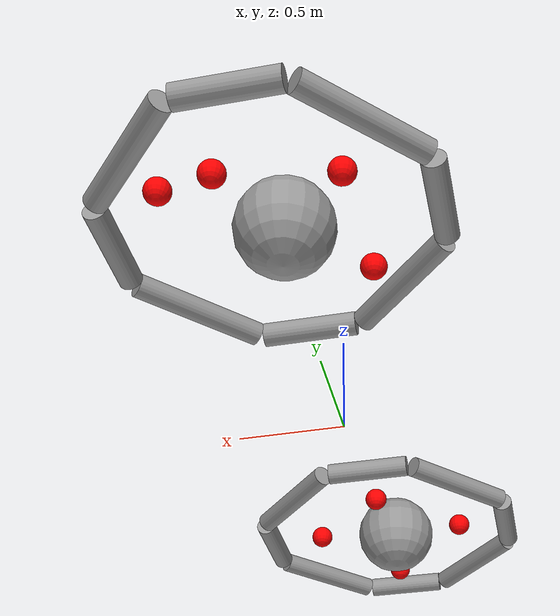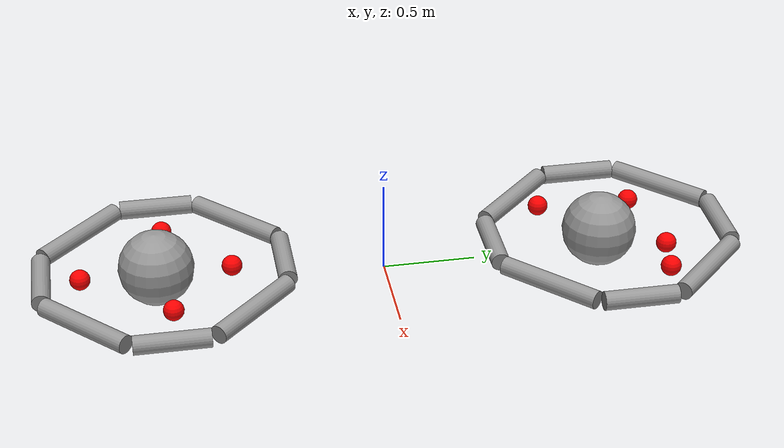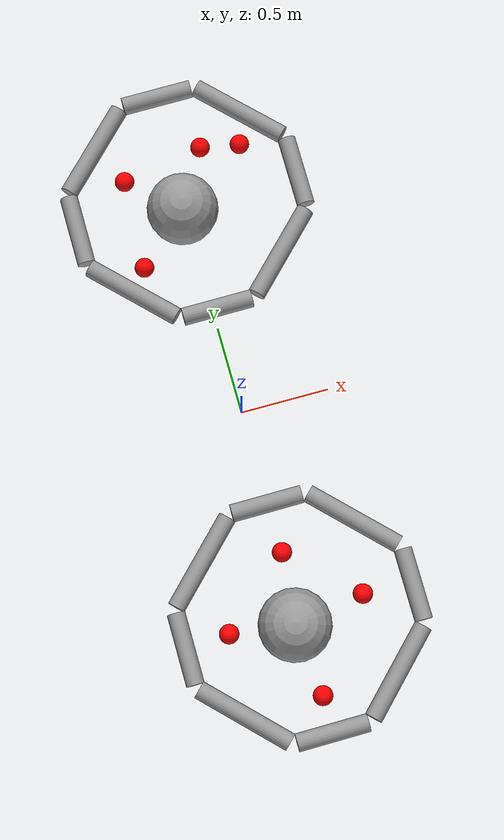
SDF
<?xml version='1.0'?>
<sdf version='1.7'>
  <model name='ocean_cleanup'>
    <model name='octagon'>
      <link name='link_4'>
        <inertial>
          <mass>1</mass>
          <inertia>
            <ixx>0.145833</ixx>
            <ixy>0</ixy>
            <ixz>0</ixz>
            <iyy>0.145833</iyy>
            <iyz>0</iyz>
            <izz>0.125</izz>
          </inertia>
          <pose>0 0 0 0 -0 0</pose>
        </inertial>
        <pose>-0.029127 0.97677 0.5 3.14159 1.57079 3.14159</pose>
        <gravity>1</gravity>
        <self_collide>0</self_collide>
        <kinematic>0</kinematic>
        <enable_wind>0</enable_wind>
        <visual name='visual'>
          <pose>0 0 0 0 -0 0</pose>
          <geometry>
            <cylinder>
              <radius>0.05</radius>
              <length>0.398068</length>
            </cylinder>
          </geometry>
          <material>
            <lighting>1</lighting>
            <script>
              <uri>file://media/materials/scripts/gazebo.material</uri>
              <name>Gazebo/Grey</name>
            </script>
            <shader type='pixel'>
              <normal_map>__default__</normal_map>
            </shader>
            <ambient>0.3 0.3 0.3 1</ambient>
            <diffuse>0.7 0.7 0.7 1</diffuse>
            <specular>0.01 0.01 0.01 1</specular>
            <emissive>0 0 0 1</emissive>
          </material>
          <transparency>0</transparency>
          <cast_shadows>1</cast_shadows>
        </visual>
        <collision name='collision'>
          <laser_retro>0</laser_retro>
          <max_contacts>10</max_contacts>
          <pose>0 0 0 0 -0 0</pose>
          <geometry>
            <cylinder>
              <radius>0.05</radius>
              <length>0.398068</length>
            </cylinder>
          </geometry>
          <surface>
            <friction>
              <ode>
                <mu>1</mu>
                <mu2>1</mu2>
                <fdir1>0 0 0</fdir1>
                <slip1>0</slip1>
                <slip2>0</slip2>
              </ode>
              <torsional>
                <coefficient>1</coefficient>
                <patch_radius>0</patch_radius>
                <surface_radius>0</surface_radius>
                <use_patch_radius>1</use_patch_radius>
                <ode>
                  <slip>0</slip>
                </ode>
              </torsional>
            </friction>
            <bounce>
              <restitution_coefficient>0</restitution_coefficient>
              <threshold>1e+06</threshold>
            </bounce>
            <contact>
              <collide_without_contact>0</collide_without_contact>
              <collide_without_contact_bitmask>1</collide_without_contact_bitmask>
              <collide_bitmask>1</collide_bitmask>
              <ode>
                <soft_cfm>0</soft_cfm>
                <soft_erp>0.2</soft_erp>
                <kp>1e+13</kp>
                <kd>1</kd>
                <max_vel>0.01</max_vel>
                <min_depth>0</min_depth>
              </ode>
              <bullet>
                <split_impulse>1</split_impulse>
                <split_impulse_penetration_threshold>-0.01</split_impulse_penetration_threshold>
                <soft_cfm>0</soft_cfm>
                <soft_erp>0.2</soft_erp>
                <kp>1e+13</kp>
                <kd>1</kd>
              </bullet>
            </contact>
          </surface>
        </collision>
      </link>
      <link name='link_4_clone'>
        <inertial>
          <mass>1</mass>
          <inertia>
            <ixx>0.145833</ixx>
            <ixy>0</ixy>
            <ixz>0</ixz>
            <iyy>0.145833</iyy>
            <iyz>0</iyz>
            <izz>0.125</izz>
          </inertia>
          <pose>0 0 0 0 -0 0</pose>
        </inertial>
        <pose>-0.02399 -0.306731 0.5 3.14159 1.57079 3.14159</pose>
        <gravity>1</gravity>
        <self_collide>0</self_collide>
        <kinematic>0</kinematic>
        <enable_wind>0</enable_wind>
        <visual name='visual'>
          <pose>0 0 0 0 -0 0</pose>
          <geometry>
            <cylinder>
              <radius>0.05</radius>
              <length>0.398068</length>
            </cylinder>
          </geometry>
          <material>
            <lighting>1</lighting>
            <script>
              <uri>file://media/materials/scripts/gazebo.material</uri>
              <name>Gazebo/Grey</name>
            </script>
            <shader type='pixel'>
              <normal_map>__default__</normal_map>
            </shader>
            <ambient>0.3 0.3 0.3 1</ambient>
            <diffuse>0.7 0.7 0.7 1</diffuse>
            <specular>0.01 0.01 0.01 1</specular>
            <emissive>0 0 0 1</emissive>
          </material>
          <transparency>0</transparency>
          <cast_shadows>1</cast_shadows>
        </visual>
        <collision name='collision'>
          <laser_retro>0</laser_retro>
          <max_contacts>10</max_contacts>
          <pose>0 0 0 0 -0 0</pose>
          <geometry>
            <cylinder>
              <radius>0.05</radius>
              <length>0.398068</length>
            </cylinder>
          </geometry>
          <surface>
            <friction>
              <ode>
                <mu>1</mu>
                <mu2>1</mu2>
                <fdir1>0 0 0</fdir1>
                <slip1>0</slip1>
                <slip2>0</slip2>
              </ode>
              <torsional>
                <coefficient>1</coefficient>
                <patch_radius>0</patch_radius>
                <surface_radius>0</surface_radius>
                <use_patch_radius>1</use_patch_radius>
                <ode>
                  <slip>0</slip>
                </ode>
              </torsional>
            </friction>
            <bounce>
              <restitution_coefficient>0</restitution_coefficient>
              <threshold>1e+06</threshold>
            </bounce>
            <contact>
              <collide_without_contact>0</collide_without_contact>
              <collide_without_contact_bitmask>1</collide_without_contact_bitmask>
              <collide_bitmask>1</collide_bitmask>
              <ode>
                <soft_cfm>0</soft_cfm>
                <soft_erp>0.2</soft_erp>
                <kp>1e+13</kp>
                <kd>1</kd>
                <max_vel>0.01</max_vel>
                <min_depth>0</min_depth>
              </ode>
              <bullet>
                <split_impulse>1</split_impulse>
                <split_impulse_penetration_threshold>-0.01</split_impulse_penetration_threshold>
                <soft_cfm>0</soft_cfm>
                <soft_erp>0.2</soft_erp>
                <kp>1e+13</kp>
                <kd>1</kd>
              </bullet>
            </contact>
          </surface>
        </collision>
      </link>
      <link name='link_4_clone_0'>
        <inertial>
          <mass>1</mass>
          <inertia>
            <ixx>0.145833</ixx>
            <ixy>0</ixy>
            <ixz>0</ixz>
            <iyy>0.145833</iyy>
            <iyz>0</iyz>
            <izz>0.125</izz>
          </inertia>
          <pose>0 0 0 0 -0 0</pose>
        </inertial>
        <pose>-0.45644 0.761979 0.5 2.35102 1.57079 3.13642</pose>
        <gravity>1</gravity>
        <self_collide>0</self_collide>
        <kinematic>0</kinematic>
        <enable_wind>0</enable_wind>
        <visual name='visual'>
          <pose>0 0 0 0 -0 0</pose>
          <geometry>
            <cylinder>
              <radius>0.05</radius>
              <length>0.562966</length>
            </cylinder>
          </geometry>
          <material>
            <lighting>1</lighting>
            <script>
              <uri>file://media/materials/scripts/gazebo.material</uri>
              <name>Gazebo/Grey</name>
            </script>
            <shader type='pixel'>
              <normal_map>__default__</normal_map>
            </shader>
            <ambient>0.3 0.3 0.3 1</ambient>
            <diffuse>0.7 0.7 0.7 1</diffuse>
            <specular>0.01 0.01 0.01 1</specular>
            <emissive>0 0 0 1</emissive>
          </material>
          <transparency>0</transparency>
          <cast_shadows>1</cast_shadows>
        </visual>
        <collision name='collision'>
          <laser_retro>0</laser_retro>
          <max_contacts>10</max_contacts>
          <pose>0 0 0 0 -0 0</pose>
          <geometry>
            <cylinder>
              <radius>0.05</radius>
              <length>0.562966</length>
            </cylinder>
          </geometry>
          <surface>
            <friction>
              <ode>
                <mu>1</mu>
                <mu2>1</mu2>
                <fdir1>0 0 0</fdir1>
                <slip1>0</slip1>
                <slip2>0</slip2>
              </ode>
              <torsional>
                <coefficient>1</coefficient>
                <patch_radius>0</patch_radius>
                <surface_radius>0</surface_radius>
                <use_patch_radius>1</use_patch_radius>
                <ode>
                  <slip>0</slip>
                </ode>
              </torsional>
            </friction>
            <bounce>
              <restitution_coefficient>0</restitution_coefficient>
              <threshold>1e+06</threshold>
            </bounce>
            <contact>
              <collide_without_contact>0</collide_without_contact>
              <collide_without_contact_bitmask>1</collide_without_contact_bitmask>
              <collide_bitmask>1</collide_bitmask>
              <ode>
                <soft_cfm>0</soft_cfm>
                <soft_erp>0.2</soft_erp>
                <kp>1e+13</kp>
                <kd>1</kd>
                <max_vel>0.01</max_vel>
                <min_depth>0</min_depth>
              </ode>
              <bullet>
                <split_impulse>1</split_impulse>
                <split_impulse_penetration_threshold>-0.01</split_impulse_penetration_threshold>
                <soft_cfm>0</soft_cfm>
                <soft_erp>0.2</soft_erp>
                <kp>1e+13</kp>
                <kd>1</kd>
              </bullet>
            </contact>
          </surface>
        </collision>
      </link>
      <link name='link_4_clone_0_clone'>
        <inertial>
          <mass>1</mass>
          <inertia>
            <ixx>0.145833</ixx>
            <ixy>0</ixy>
            <ixz>0</ixz>
            <iyy>0.145833</iyy>
            <iyz>0</iyz>
            <izz>0.125</izz>
          </inertia>
          <pose>0 0 0 0 -0 0</pose>
        </inertial>
        <pose>0.406078 -0.092853 0.499999 2.35102 1.57079 3.13642</pose>
        <gravity>1</gravity>
        <self_collide>0</self_collide>
        <kinematic>0</kinematic>
        <enable_wind>0</enable_wind>
        <visual name='visual'>
          <pose>0 0 0 0 -0 0</pose>
          <geometry>
            <cylinder>
              <radius>0.05</radius>
              <length>0.562966</length>
            </cylinder>
          </geometry>
          <material>
            <lighting>1</lighting>
            <script>
              <uri>file://media/materials/scripts/gazebo.material</uri>
              <name>Gazebo/Grey</name>
            </script>
            <shader type='pixel'>
              <normal_map>__default__</normal_map>
            </shader>
            <ambient>0.3 0.3 0.3 1</ambient>
            <diffuse>0.7 0.7 0.7 1</diffuse>
            <specular>0.01 0.01 0.01 1</specular>
            <emissive>0 0 0 1</emissive>
          </material>
          <transparency>0</transparency>
          <cast_shadows>1</cast_shadows>
        </visual>
        <collision name='collision'>
          <laser_retro>0</laser_retro>
          <max_contacts>10</max_contacts>
          <pose>0 0 0 0 -0 0</pose>
          <geometry>
            <cylinder>
              <radius>0.05</radius>
              <length>0.562966</length>
            </cylinder>
          </geometry>
          <surface>
            <friction>
              <ode>
                <mu>1</mu>
                <mu2>1</mu2>
                <fdir1>0 0 0</fdir1>
                <slip1>0</slip1>
                <slip2>0</slip2>
              </ode>
              <torsional>
                <coefficient>1</coefficient>
                <patch_radius>0</patch_radius>
                <surface_radius>0</surface_radius>
                <use_patch_radius>1</use_patch_radius>
                <ode>
                  <slip>0</slip>
                </ode>
              </torsional>
            </friction>
            <bounce>
              <restitution_coefficient>0</restitution_coefficient>
              <threshold>1e+06</threshold>
            </bounce>
            <contact>
              <collide_without_contact>0</collide_without_contact>
              <collide_without_contact_bitmask>1</collide_without_contact_bitmask>
              <collide_bitmask>1</collide_bitmask>
              <ode>
                <soft_cfm>0</soft_cfm>
                <soft_erp>0.2</soft_erp>
                <kp>1e+13</kp>
                <kd>1</kd>
                <max_vel>0.01</max_vel>
                <min_depth>0</min_depth>
              </ode>
              <bullet>
                <split_impulse>1</split_impulse>
                <split_impulse_penetration_threshold>-0.01</split_impulse_penetration_threshold>
                <soft_cfm>0</soft_cfm>
                <soft_erp>0.2</soft_erp>
                <kp>1e+13</kp>
                <kd>1</kd>
              </bullet>
            </contact>
          </surface>
        </collision>
      </link>
      <link name='link_4_clone_0_clone_0'>
        <inertial>
          <mass>1</mass>
          <inertia>
            <ixx>0.145833</ixx>
            <ixy>0</ixy>
            <ixz>0</ixz>
            <iyy>0.145833</iyy>
            <iyz>0</iyz>
            <izz>0.125</izz>
          </inertia>
          <pose>0 0 0 0 -0 0</pose>
        </inertial>
        <pose>-0.454744 -0.094458 0.5 0.786985 1.57079 3.13801</pose>
        <gravity>1</gravity>
        <self_collide>0</self_collide>
        <kinematic>0</kinematic>
        <enable_wind>0</enable_wind>
        <visual name='visual'>
          <pose>0 0 0 0 -0 0</pose>
          <geometry>
            <cylinder>
              <radius>0.05</radius>
              <length>0.562966</length>
            </cylinder>
          </geometry>
          <material>
            <lighting>1</lighting>
            <script>
              <uri>file://media/materials/scripts/gazebo.material</uri>
              <name>Gazebo/Grey</name>
            </script>
            <shader type='pixel'>
              <normal_map>__default__</normal_map>
            </shader>
            <ambient>0.3 0.3 0.3 1</ambient>
            <diffuse>0.7 0.7 0.7 1</diffuse>
            <specular>0.01 0.01 0.01 1</specular>
            <emissive>0 0 0 1</emissive>
          </material>
          <transparency>0</transparency>
          <cast_shadows>1</cast_shadows>
        </visual>
        <collision name='collision'>
          <laser_retro>0</laser_retro>
          <max_contacts>10</max_contacts>
          <pose>0 0 0 0 -0 0</pose>
          <geometry>
            <cylinder>
              <radius>0.05</radius>
              <length>0.562966</length>
            </cylinder>
          </geometry>
          <surface>
            <friction>
              <ode>
                <mu>1</mu>
                <mu2>1</mu2>
                <fdir1>0 0 0</fdir1>
                <slip1>0</slip1>
                <slip2>0</slip2>
              </ode>
              <torsional>
                <coefficient>1</coefficient>
                <patch_radius>0</patch_radius>
                <surface_radius>0</surface_radius>
                <use_patch_radius>1</use_patch_radius>
                <ode>
                  <slip>0</slip>
                </ode>
              </torsional>
            </friction>
            <bounce>
              <restitution_coefficient>0</restitution_coefficient>
              <threshold>1e+06</threshold>
            </bounce>
            <contact>
              <collide_without_contact>0</collide_without_contact>
              <collide_without_contact_bitmask>1</collide_without_contact_bitmask>
              <collide_bitmask>1</collide_bitmask>
              <ode>
                <soft_cfm>0</soft_cfm>
                <soft_erp>0.2</soft_erp>
                <kp>1e+13</kp>
                <kd>1</kd>
                <max_vel>0.01</max_vel>
                <min_depth>0</min_depth>
              </ode>
              <bullet>
                <split_impulse>1</split_impulse>
                <split_impulse_penetration_threshold>-0.01</split_impulse_penetration_threshold>
                <soft_cfm>0</soft_cfm>
                <soft_erp>0.2</soft_erp>
                <kp>1e+13</kp>
                <kd>1</kd>
              </bullet>
            </contact>
          </surface>
        </collision>
      </link>
      <link name='link_4_clone_0_clone_0_clone'>
        <inertial>
          <mass>1</mass>
          <inertia>
            <ixx>0.145833</ixx>
            <ixy>0</ixy>
            <ixz>0</ixz>
            <iyy>0.145833</iyy>
            <iyz>0</iyz>
            <izz>0.125</izz>
          </inertia>
          <pose>0 0 0 0 -0 0</pose>
        </inertial>
        <pose>0.40382 0.769921 0.5 0.786985 1.57079 3.13801</pose>
        <gravity>1</gravity>
        <self_collide>0</self_collide>
        <kinematic>0</kinematic>
        <enable_wind>0</enable_wind>
        <visual name='visual'>
          <pose>0 0 0 0 -0 0</pose>
          <geometry>
            <cylinder>
              <radius>0.05</radius>
              <length>0.562966</length>
            </cylinder>
          </geometry>
          <material>
            <lighting>1</lighting>
            <script>
              <uri>file://media/materials/scripts/gazebo.material</uri>
              <name>Gazebo/Grey</name>
            </script>
            <shader type='pixel'>
              <normal_map>__default__</normal_map>
            </shader>
            <ambient>0.3 0.3 0.3 1</ambient>
            <diffuse>0.7 0.7 0.7 1</diffuse>
            <specular>0.01 0.01 0.01 1</specular>
            <emissive>0 0 0 1</emissive>
          </material>
          <transparency>0</transparency>
          <cast_shadows>1</cast_shadows>
        </visual>
        <collision name='collision'>
          <laser_retro>0</laser_retro>
          <max_contacts>10</max_contacts>
          <pose>0 0 0 0 -0 0</pose>
          <geometry>
            <cylinder>
              <radius>0.05</radius>
              <length>0.562966</length>
            </cylinder>
          </geometry>
          <surface>
            <friction>
              <ode>
                <mu>1</mu>
                <mu2>1</mu2>
                <fdir1>0 0 0</fdir1>
                <slip1>0</slip1>
                <slip2>0</slip2>
              </ode>
              <torsional>
                <coefficient>1</coefficient>
                <patch_radius>0</patch_radius>
                <surface_radius>0</surface_radius>
                <use_patch_radius>1</use_patch_radius>
                <ode>
                  <slip>0</slip>
                </ode>
              </torsional>
            </friction>
            <bounce>
              <restitution_coefficient>0</restitution_coefficient>
              <threshold>1e+06</threshold>
            </bounce>
            <contact>
              <collide_without_contact>0</collide_without_contact>
              <collide_without_contact_bitmask>1</collide_without_contact_bitmask>
              <collide_bitmask>1</collide_bitmask>
              <ode>
                <soft_cfm>0</soft_cfm>
                <soft_erp>0.2</soft_erp>
                <kp>1e+13</kp>
                <kd>1</kd>
                <max_vel>0.01</max_vel>
                <min_depth>0</min_depth>
              </ode>
              <bullet>
                <split_impulse>1</split_impulse>
                <split_impulse_penetration_threshold>-0.01</split_impulse_penetration_threshold>
                <soft_cfm>0</soft_cfm>
                <soft_erp>0.2</soft_erp>
                <kp>1e+13</kp>
                <kd>1</kd>
              </bullet>
            </contact>
          </surface>
        </collision>
      </link>
      <link name='link_4_clone_1'>
        <inertial>
          <mass>1</mass>
          <inertia>
            <ixx>0.145833</ixx>
            <ixy>0</ixy>
            <ixz>0</ixz>
            <iyy>0.145833</iyy>
            <iyz>0</iyz>
            <izz>0.125</izz>
          </inertia>
          <pose>0 0 0 0 -0 0</pose>
        </inertial>
        <pose>-0.665422 0.33412 0.500002 1.5708 1.57079 3.14159</pose>
        <gravity>1</gravity>
        <self_collide>0</self_collide>
        <kinematic>0</kinematic>
        <enable_wind>0</enable_wind>
        <visual name='visual'>
          <pose>0 0 0 0 -0 0</pose>
          <geometry>
            <cylinder>
              <radius>0.05</radius>
              <length>0.398068</length>
            </cylinder>
          </geometry>
          <material>
            <lighting>1</lighting>
            <script>
              <uri>file://media/materials/scripts/gazebo.material</uri>
              <name>Gazebo/Grey</name>
            </script>
            <shader type='pixel'>
              <normal_map>__default__</normal_map>
            </shader>
            <ambient>0.3 0.3 0.3 1</ambient>
            <diffuse>0.7 0.7 0.7 1</diffuse>
            <specular>0.01 0.01 0.01 1</specular>
            <emissive>0 0 0 1</emissive>
          </material>
          <transparency>0</transparency>
          <cast_shadows>1</cast_shadows>
        </visual>
        <collision name='collision'>
          <laser_retro>0</laser_retro>
          <max_contacts>10</max_contacts>
          <pose>0 0 0 0 -0 0</pose>
          <geometry>
            <cylinder>
              <radius>0.05</radius>
              <length>0.398068</length>
            </cylinder>
          </geometry>
          <surface>
            <friction>
              <ode>
                <mu>1</mu>
                <mu2>1</mu2>
                <fdir1>0 0 0</fdir1>
                <slip1>0</slip1>
                <slip2>0</slip2>
              </ode>
              <torsional>
                <coefficient>1</coefficient>
                <patch_radius>0</patch_radius>
                <surface_radius>0</surface_radius>
                <use_patch_radius>1</use_patch_radius>
                <ode>
                  <slip>0</slip>
                </ode>
              </torsional>
            </friction>
            <bounce>
              <restitution_coefficient>0</restitution_coefficient>
              <threshold>1e+06</threshold>
            </bounce>
            <contact>
              <collide_without_contact>0</collide_without_contact>
              <collide_without_contact_bitmask>1</collide_without_contact_bitmask>
              <collide_bitmask>1</collide_bitmask>
              <ode>
                <soft_cfm>0</soft_cfm>
                <soft_erp>0.2</soft_erp>
                <kp>1e+13</kp>
                <kd>1</kd>
                <max_vel>0.01</max_vel>
                <min_depth>0</min_depth>
              </ode>
              <bullet>
                <split_impulse>1</split_impulse>
                <split_impulse_penetration_threshold>-0.01</split_impulse_penetration_threshold>
                <soft_cfm>0</soft_cfm>
                <soft_erp>0.2</soft_erp>
                <kp>1e+13</kp>
                <kd>1</kd>
              </bullet>
            </contact>
          </surface>
        </collision>
      </link>
      <link name='link_4_clone_1_clone'>
        <inertial>
          <mass>1</mass>
          <inertia>
            <ixx>0.145833</ixx>
            <ixy>0</ixy>
            <ixz>0</ixz>
            <iyy>0.145833</iyy>
            <iyz>0</iyz>
            <izz>0.125</izz>
          </inertia>
          <pose>0 0 0 0 -0 0</pose>
        </inertial>
        <pose>0.618286 0.337066 0.5 1.5708 1.57079 3.14159</pose>
        <gravity>1</gravity>
        <self_collide>0</self_collide>
        <kinematic>0</kinematic>
        <enable_wind>0</enable_wind>
        <visual name='visual'>
          <pose>0 0 0 0 -0 0</pose>
          <geometry>
            <cylinder>
              <radius>0.05</radius>
              <length>0.398068</length>
            </cylinder>
          </geometry>
          <material>
            <lighting>1</lighting>
            <script>
              <uri>file://media/materials/scripts/gazebo.material</uri>
              <name>Gazebo/Grey</name>
            </script>
            <shader type='pixel'>
              <normal_map>__default__</normal_map>
            </shader>
            <ambient>0.3 0.3 0.3 1</ambient>
            <diffuse>0.7 0.7 0.7 1</diffuse>
            <specular>0.01 0.01 0.01 1</specular>
            <emissive>0 0 0 1</emissive>
          </material>
          <transparency>0</transparency>
          <cast_shadows>1</cast_shadows>
        </visual>
        <collision name='collision'>
          <laser_retro>0</laser_retro>
          <max_contacts>10</max_contacts>
          <pose>0 0 0 0 -0 0</pose>
          <geometry>
            <cylinder>
              <radius>0.05</radius>
              <length>0.398068</length>
            </cylinder>
          </geometry>
          <surface>
            <friction>
              <ode>
                <mu>1</mu>
                <mu2>1</mu2>
                <fdir1>0 0 0</fdir1>
                <slip1>0</slip1>
                <slip2>0</slip2>
              </ode>
              <torsional>
                <coefficient>1</coefficient>
                <patch_radius>0</patch_radius>
                <surface_radius>0</surface_radius>
                <use_patch_radius>1</use_patch_radius>
                <ode>
                  <slip>0</slip>
                </ode>
              </torsional>
            </friction>
            <bounce>
              <restitution_coefficient>0</restitution_coefficient>
              <threshold>1e+06</threshold>
            </bounce>
            <contact>
              <collide_without_contact>0</collide_without_contact>
              <collide_without_contact_bitmask>1</collide_without_contact_bitmask>
              <collide_bitmask>1</collide_bitmask>
              <ode>
                <soft_cfm>0</soft_cfm>
                <soft_erp>0.2</soft_erp>
                <kp>1e+13</kp>
                <kd>1</kd>
                <max_vel>0.01</max_vel>
                <min_depth>0</min_depth>
              </ode>
              <bullet>
                <split_impulse>1</split_impulse>
                <split_impulse_penetration_threshold>-0.01</split_impulse_penetration_threshold>
                <soft_cfm>0</soft_cfm>
                <soft_erp>0.2</soft_erp>
                <kp>1e+13</kp>
                <kd>1</kd>
              </bullet>
            </contact>
          </surface>
        </collision>
      </link>
      <link name='link_5'>
        <inertial>
          <mass>0.130267</mass>
          <inertia>
            <ixx>0.00055181</ixx>
            <ixy>0</ixy>
            <ixz>0</ixz>
            <iyy>0.00055181</iyy>
            <iyz>0</iyz>
            <izz>0.00055181</izz>
          </inertia>
          <pose>0 0 0 0 -0 0</pose>
        </inertial>
        <pose>-0.060768 0.298874 0.5 0 -0 0</pose>
        <gravity>1</gravity>
        <self_collide>0</self_collide>
        <kinematic>0</kinematic>
        <enable_wind>0</enable_wind>
        <visual name='visual'>
          <pose>0 0 0 0 -0 0</pose>
          <geometry>
            <sphere>
              <radius>0.202999</radius>
            </sphere>
          </geometry>
          <material>
            <lighting>1</lighting>
            <script>
              <uri>file://media/materials/scripts/gazebo.material</uri>
              <name>Gazebo/Grey</name>
            </script>
            <shader type='pixel'>
              <normal_map>__default__</normal_map>
            </shader>
            <ambient>0 0 0 1</ambient>
            <diffuse>0 0 0 1</diffuse>
            <specular>0 0 0 1</specular>
            <emissive>0 0 0 1</emissive>
          </material>
          <transparency>0</transparency>
          <cast_shadows>1</cast_shadows>
        </visual>
        <collision name='collision'>
          <laser_retro>0</laser_retro>
          <max_contacts>10</max_contacts>
          <pose>0 0 0 0 -0 0</pose>
          <geometry>
            <sphere>
              <radius>0.202999</radius>
            </sphere>
          </geometry>
          <surface>
            <friction>
              <ode>
                <mu>1</mu>
                <mu2>1</mu2>
                <fdir1>0 0 0</fdir1>
                <slip1>0</slip1>
                <slip2>0</slip2>
              </ode>
              <torsional>
                <coefficient>1</coefficient>
                <patch_radius>0</patch_radius>
                <surface_radius>0</surface_radius>
                <use_patch_radius>1</use_patch_radius>
                <ode>
                  <slip>0</slip>
                </ode>
              </torsional>
            </friction>
            <bounce>
              <restitution_coefficient>0</restitution_coefficient>
              <threshold>1e+06</threshold>
            </bounce>
            <contact>
              <collide_without_contact>0</collide_without_contact>
              <collide_without_contact_bitmask>1</collide_without_contact_bitmask>
              <collide_bitmask>1</collide_bitmask>
              <ode>
                <soft_cfm>0</soft_cfm>
                <soft_erp>0.2</soft_erp>
                <kp>1e+13</kp>
                <kd>1</kd>
                <max_vel>0.01</max_vel>
                <min_depth>0</min_depth>
              </ode>
              <bullet>
                <split_impulse>1</split_impulse>
                <split_impulse_penetration_threshold>-0.01</split_impulse_penetration_threshold>
                <soft_cfm>0</soft_cfm>
                <soft_erp>0.2</soft_erp>
                <kp>1e+13</kp>
                <kd>1</kd>
              </bullet>
            </contact>
          </surface>
        </collision>
      </link>
      <joint name='link_5_JOINT_10' type='fixed'>
        <parent>link_5</parent>
        <child>link_4_clone_0</child>
        <pose>0 0 0 0 -0 0</pose>
        <physics>
          <ode>
            <limit>
              <cfm>0</cfm>
              <erp>0.2</erp>
            </limit>
            <suspension>
              <cfm>0</cfm>
              <erp>0.2</erp>
            </suspension>
          </ode>
        </physics>
      </joint>
      <joint name='link_5_JOINT_11' type='fixed'>
        <parent>link_5</parent>
        <child>link_4</child>
        <pose>0 0 0 0 -0 0</pose>
        <physics>
          <ode>
            <limit>
              <cfm>0</cfm>
              <erp>0.2</erp>
            </limit>
            <suspension>
              <cfm>0</cfm>
              <erp>0.2</erp>
            </suspension>
          </ode>
        </physics>
      </joint>
      <joint name='link_5_JOINT_12' type='fixed'>
        <parent>link_5</parent>
        <child>link_4_clone_0_clone_0_clone</child>
        <pose>0 0 0 0 -0 0</pose>
        <physics>
          <ode>
            <limit>
              <cfm>0</cfm>
              <erp>0.2</erp>
            </limit>
            <suspension>
              <cfm>0</cfm>
              <erp>0.2</erp>
            </suspension>
          </ode>
        </physics>
      </joint>
      <joint name='link_5_JOINT_13' type='fixed'>
        <parent>link_5</parent>
        <child>link_4_clone_1_clone</child>
        <pose>0 0 0 0 -0 0</pose>
        <physics>
          <ode>
            <limit>
              <cfm>0</cfm>
              <erp>0.2</erp>
            </limit>
            <suspension>
              <cfm>0</cfm>
              <erp>0.2</erp>
            </suspension>
          </ode>
        </physics>
      </joint>
      <joint name='link_5_JOINT_14' type='fixed'>
        <parent>link_5</parent>
        <child>link_4_clone_0_clone</child>
        <pose>0 0 0 0 -0 0</pose>
        <physics>
          <ode>
            <limit>
              <cfm>0</cfm>
              <erp>0.2</erp>
            </limit>
            <suspension>
              <cfm>0</cfm>
              <erp>0.2</erp>
            </suspension>
          </ode>
        </physics>
      </joint>
      <joint name='link_5_JOINT_15' type='fixed'>
        <parent>link_5</parent>
        <child>link_4_clone</child>
        <pose>0 0 0 0 -0 0</pose>
        <physics>
          <ode>
            <limit>
              <cfm>0</cfm>
              <erp>0.2</erp>
            </limit>
            <suspension>
              <cfm>0</cfm>
              <erp>0.2</erp>
            </suspension>
          </ode>
        </physics>
      </joint>
      <joint name='link_5_JOINT_8' type='fixed'>
        <parent>link_5</parent>
        <child>link_4_clone_0_clone_0</child>
        <pose>0 0 0 0 -0 0</pose>
        <physics>
          <ode>
            <limit>
              <cfm>0</cfm>
              <erp>0.2</erp>
            </limit>
            <suspension>
              <cfm>0</cfm>
              <erp>0.2</erp>
            </suspension>
          </ode>
        </physics>
      </joint>
      <joint name='link_5_JOINT_9' type='fixed'>
        <parent>link_5</parent>
        <child>link_4_clone_1</child>
        <pose>0 0 0 0 -0 0</pose>
        <physics>
          <ode>
            <limit>
              <cfm>0</cfm>
              <erp>0.2</erp>
            </limit>
            <suspension>
              <cfm>0</cfm>
              <erp>0.2</erp>
            </suspension>
          </ode>
        </physics>
      </joint>
      <static>0</static>
      <allow_auto_disable>1</allow_auto_disable>
      <pose>0.048737 0.902336 -0.395137 0 -0 0</pose>
    </model>
    <model name='octagon_clone'>
      <link name='link_4'>
        <inertial>
          <mass>1</mass>
          <inertia>
            <ixx>0.145833</ixx>
            <ixy>0</ixy>
            <ixz>0</ixz>
            <iyy>0.145833</iyy>
            <iyz>0</iyz>
            <izz>0.125</izz>
          </inertia>
          <pose>0 0 0 0 -0 0</pose>
        </inertial>
        <pose>-0.029127 0.97677 0.5 3.14159 1.57079 3.14159</pose>
        <gravity>1</gravity>
        <self_collide>0</self_collide>
        <kinematic>0</kinematic>
        <enable_wind>0</enable_wind>
        <visual name='visual'>
          <pose>0 0 0 0 -0 0</pose>
          <geometry>
            <cylinder>
              <radius>0.05</radius>
              <length>0.398068</length>
            </cylinder>
          </geometry>
          <material>
            <lighting>1</lighting>
            <script>
              <uri>file://media/materials/scripts/gazebo.material</uri>
              <name>Gazebo/Grey</name>
            </script>
            <shader type='pixel'>
              <normal_map>__default__</normal_map>
            </shader>
            <ambient>0.3 0.3 0.3 1</ambient>
            <diffuse>0.7 0.7 0.7 1</diffuse>
            <specular>0.01 0.01 0.01 1</specular>
            <emissive>0 0 0 1</emissive>
          </material>
          <transparency>0</transparency>
          <cast_shadows>1</cast_shadows>
        </visual>
        <collision name='collision'>
          <laser_retro>0</laser_retro>
          <max_contacts>10</max_contacts>
          <pose>0 0 0 0 -0 0</pose>
          <geometry>
            <cylinder>
              <radius>0.05</radius>
              <length>0.398068</length>
            </cylinder>
          </geometry>
          <surface>
            <friction>
              <ode>
                <mu>1</mu>
                <mu2>1</mu2>
                <fdir1>0 0 0</fdir1>
                <slip1>0</slip1>
                <slip2>0</slip2>
              </ode>
              <torsional>
                <coefficient>1</coefficient>
                <patch_radius>0</patch_radius>
                <surface_radius>0</surface_radius>
                <use_patch_radius>1</use_patch_radius>
                <ode>
                  <slip>0</slip>
                </ode>
              </torsional>
            </friction>
            <bounce>
              <restitution_coefficient>0</restitution_coefficient>
              <threshold>1e+06</threshold>
            </bounce>
            <contact>
              <collide_without_contact>0</collide_without_contact>
              <collide_without_contact_bitmask>1</collide_without_contact_bitmask>
              <collide_bitmask>1</collide_bitmask>
              <ode>
                <soft_cfm>0</soft_cfm>
                <soft_erp>0.2</soft_erp>
                <kp>1e+13</kp>
                <kd>1</kd>
                <max_vel>0.01</max_vel>
                <min_depth>0</min_depth>
              </ode>
              <bullet>
                <split_impulse>1</split_impulse>
                <split_impulse_penetration_threshold>-0.01</split_impulse_penetration_threshold>
                <soft_cfm>0</soft_cfm>
                <soft_erp>0.2</soft_erp>
                <kp>1e+13</kp>
                <kd>1</kd>
              </bullet>
            </contact>
          </surface>
        </collision>
      </link>
      <link name='link_4_clone'>
        <inertial>
          <mass>1</mass>
          <inertia>
            <ixx>0.145833</ixx>
            <ixy>0</ixy>
            <ixz>0</ixz>
            <iyy>0.145833</iyy>
            <iyz>0</iyz>
            <izz>0.125</izz>
          </inertia>
          <pose>0 0 0 0 -0 0</pose>
        </inertial>
        <pose>-0.02399 -0.306731 0.5 3.14159 1.57079 3.14159</pose>
        <gravity>1</gravity>
        <self_collide>0</self_collide>
        <kinematic>0</kinematic>
        <enable_wind>0</enable_wind>
        <visual name='visual'>
          <pose>0 0 0 0 -0 0</pose>
          <geometry>
            <cylinder>
              <radius>0.05</radius>
              <length>0.398068</length>
            </cylinder>
          </geometry>
          <material>
            <lighting>1</lighting>
            <script>
              <uri>file://media/materials/scripts/gazebo.material</uri>
              <name>Gazebo/Grey</name>
            </script>
            <shader type='pixel'>
              <normal_map>__default__</normal_map>
            </shader>
            <ambient>0.3 0.3 0.3 1</ambient>
            <diffuse>0.7 0.7 0.7 1</diffuse>
            <specular>0.01 0.01 0.01 1</specular>
            <emissive>0 0 0 1</emissive>
          </material>
          <transparency>0</transparency>
          <cast_shadows>1</cast_shadows>
        </visual>
        <collision name='collision'>
          <laser_retro>0</laser_retro>
          <max_contacts>10</max_contacts>
          <pose>0 0 0 0 -0 0</pose>
          <geometry>
            <cylinder>
              <radius>0.05</radius>
              <length>0.398068</length>
            </cylinder>
          </geometry>
          <surface>
            <friction>
              <ode>
                <mu>1</mu>
                <mu2>1</mu2>
                <fdir1>0 0 0</fdir1>
                <slip1>0</slip1>
                <slip2>0</slip2>
              </ode>
              <torsional>
                <coefficient>1</coefficient>
                <patch_radius>0</patch_radius>
                <surface_radius>0</surface_radius>
                <use_patch_radius>1</use_patch_radius>
                <ode>
                  <slip>0</slip>
                </ode>
              </torsional>
            </friction>
            <bounce>
              <restitution_coefficient>0</restitution_coefficient>
              <threshold>1e+06</threshold>
            </bounce>
            <contact>
              <collide_without_contact>0</collide_without_contact>
              <collide_without_contact_bitmask>1</collide_without_contact_bitmask>
              <collide_bitmask>1</collide_bitmask>
              <ode>
                <soft_cfm>0</soft_cfm>
                <soft_erp>0.2</soft_erp>
                <kp>1e+13</kp>
                <kd>1</kd>
                <max_vel>0.01</max_vel>
                <min_depth>0</min_depth>
              </ode>
              <bullet>
                <split_impulse>1</split_impulse>
                <split_impulse_penetration_threshold>-0.01</split_impulse_penetration_threshold>
                <soft_cfm>0</soft_cfm>
                <soft_erp>0.2</soft_erp>
                <kp>1e+13</kp>
                <kd>1</kd>
              </bullet>
            </contact>
          </surface>
        </collision>
      </link>
      <link name='link_4_clone_0'>
        <inertial>
          <mass>1</mass>
          <inertia>
            <ixx>0.145833</ixx>
            <ixy>0</ixy>
            <ixz>0</ixz>
            <iyy>0.145833</iyy>
            <iyz>0</iyz>
            <izz>0.125</izz>
          </inertia>
          <pose>0 0 0 0 -0 0</pose>
        </inertial>
        <pose>-0.45644 0.761979 0.5 2.35102 1.57079 3.13642</pose>
        <gravity>1</gravity>
        <self_collide>0</self_collide>
        <kinematic>0</kinematic>
        <enable_wind>0</enable_wind>
        <visual name='visual'>
          <pose>0 0 0 0 -0 0</pose>
          <geometry>
            <cylinder>
              <radius>0.05</radius>
              <length>0.562966</length>
            </cylinder>
          </geometry>
          <material>
            <lighting>1</lighting>
            <script>
              <uri>file://media/materials/scripts/gazebo.material</uri>
              <name>Gazebo/Grey</name>
            </script>
            <shader type='pixel'>
              <normal_map>__default__</normal_map>
            </shader>
            <ambient>0.3 0.3 0.3 1</ambient>
            <diffuse>0.7 0.7 0.7 1</diffuse>
            <specular>0.01 0.01 0.01 1</specular>
            <emissive>0 0 0 1</emissive>
          </material>
          <transparency>0</transparency>
          <cast_shadows>1</cast_shadows>
        </visual>
        <collision name='collision'>
          <laser_retro>0</laser_retro>
          <max_contacts>10</max_contacts>
          <pose>0 0 0 0 -0 0</pose>
          <geometry>
            <cylinder>
              <radius>0.05</radius>
              <length>0.562966</length>
            </cylinder>
          </geometry>
          <surface>
            <friction>
              <ode>
                <mu>1</mu>
                <mu2>1</mu2>
                <fdir1>0 0 0</fdir1>
                <slip1>0</slip1>
                <slip2>0</slip2>
              </ode>
              <torsional>
                <coefficient>1</coefficient>
                <patch_radius>0</patch_radius>
                <surface_radius>0</surface_radius>
                <use_patch_radius>1</use_patch_radius>
                <ode>
                  <slip>0</slip>
                </ode>
              </torsional>
            </friction>
            <bounce>
              <restitution_coefficient>0</restitution_coefficient>
              <threshold>1e+06</threshold>
            </bounce>
            <contact>
              <collide_without_contact>0</collide_without_contact>
              <collide_without_contact_bitmask>1</collide_without_contact_bitmask>
              <collide_bitmask>1</collide_bitmask>
              <ode>
                <soft_cfm>0</soft_cfm>
                <soft_erp>0.2</soft_erp>
                <kp>1e+13</kp>
                <kd>1</kd>
                <max_vel>0.01</max_vel>
                <min_depth>0</min_depth>
              </ode>
              <bullet>
                <split_impulse>1</split_impulse>
                <split_impulse_penetration_threshold>-0.01</split_impulse_penetration_threshold>
                <soft_cfm>0</soft_cfm>
                <soft_erp>0.2</soft_erp>
                <kp>1e+13</kp>
                <kd>1</kd>
              </bullet>
            </contact>
          </surface>
        </collision>
      </link>
      <link name='link_4_clone_0_clone'>
        <inertial>
          <mass>1</mass>
          <inertia>
            <ixx>0.145833</ixx>
            <ixy>0</ixy>
            <ixz>0</ixz>
            <iyy>0.145833</iyy>
            <iyz>0</iyz>
            <izz>0.125</izz>
          </inertia>
          <pose>0 0 0 0 -0 0</pose>
        </inertial>
        <pose>0.406078 -0.092853 0.499999 2.35102 1.57079 3.13642</pose>
        <gravity>1</gravity>
        <self_collide>0</self_collide>
        <kinematic>0</kinematic>
        <enable_wind>0</enable_wind>
        <visual name='visual'>
          <pose>0 0 0 0 -0 0</pose>
          <geometry>
            <cylinder>
              <radius>0.05</radius>
              <length>0.562966</length>
            </cylinder>
          </geometry>
          <material>
            <lighting>1</lighting>
            <script>
              <uri>file://media/materials/scripts/gazebo.material</uri>
              <name>Gazebo/Grey</name>
            </script>
            <shader type='pixel'>
              <normal_map>__default__</normal_map>
            </shader>
            <ambient>0.3 0.3 0.3 1</ambient>
            <diffuse>0.7 0.7 0.7 1</diffuse>
            <specular>0.01 0.01 0.01 1</specular>
            <emissive>0 0 0 1</emissive>
          </material>
          <transparency>0</transparency>
          <cast_shadows>1</cast_shadows>
        </visual>
        <collision name='collision'>
          <laser_retro>0</laser_retro>
          <max_contacts>10</max_contacts>
          <pose>0 0 0 0 -0 0</pose>
          <geometry>
            <cylinder>
              <radius>0.05</radius>
              <length>0.562966</length>
            </cylinder>
          </geometry>
          <surface>
            <friction>
              <ode>
                <mu>1</mu>
                <mu2>1</mu2>
                <fdir1>0 0 0</fdir1>
                <slip1>0</slip1>
                <slip2>0</slip2>
              </ode>
              <torsional>
                <coefficient>1</coefficient>
                <patch_radius>0</patch_radius>
                <surface_radius>0</surface_radius>
                <use_patch_radius>1</use_patch_radius>
                <ode>
                  <slip>0</slip>
                </ode>
              </torsional>
            </friction>
            <bounce>
              <restitution_coefficient>0</restitution_coefficient>
              <threshold>1e+06</threshold>
            </bounce>
            <contact>
              <collide_without_contact>0</collide_without_contact>
              <collide_without_contact_bitmask>1</collide_without_contact_bitmask>
              <collide_bitmask>1</collide_bitmask>
              <ode>
                <soft_cfm>0</soft_cfm>
                <soft_erp>0.2</soft_erp>
                <kp>1e+13</kp>
                <kd>1</kd>
                <max_vel>0.01</max_vel>
                <min_depth>0</min_depth>
              </ode>
              <bullet>
                <split_impulse>1</split_impulse>
                <split_impulse_penetration_threshold>-0.01</split_impulse_penetration_threshold>
                <soft_cfm>0</soft_cfm>
                <soft_erp>0.2</soft_erp>
                <kp>1e+13</kp>
                <kd>1</kd>
              </bullet>
            </contact>
          </surface>
        </collision>
      </link>
      <link name='link_4_clone_0_clone_0'>
        <inertial>
          <mass>1</mass>
          <inertia>
            <ixx>0.145833</ixx>
            <ixy>0</ixy>
            <ixz>0</ixz>
            <iyy>0.145833</iyy>
            <iyz>0</iyz>
            <izz>0.125</izz>
          </inertia>
          <pose>0 0 0 0 -0 0</pose>
        </inertial>
        <pose>-0.454744 -0.094458 0.5 0.786985 1.57079 3.13801</pose>
        <gravity>1</gravity>
        <self_collide>0</self_collide>
        <kinematic>0</kinematic>
        <enable_wind>0</enable_wind>
        <visual name='visual'>
          <pose>0 0 0 0 -0 0</pose>
          <geometry>
            <cylinder>
              <radius>0.05</radius>
              <length>0.562966</length>
            </cylinder>
          </geometry>
          <material>
            <lighting>1</lighting>
            <script>
              <uri>file://media/materials/scripts/gazebo.material</uri>
              <name>Gazebo/Grey</name>
            </script>
            <shader type='pixel'>
              <normal_map>__default__</normal_map>
            </shader>
            <ambient>0.3 0.3 0.3 1</ambient>
            <diffuse>0.7 0.7 0.7 1</diffuse>
            <specular>0.01 0.01 0.01 1</specular>
            <emissive>0 0 0 1</emissive>
          </material>
          <transparency>0</transparency>
          <cast_shadows>1</cast_shadows>
        </visual>
        <collision name='collision'>
          <laser_retro>0</laser_retro>
          <max_contacts>10</max_contacts>
          <pose>0 0 0 0 -0 0</pose>
          <geometry>
            <cylinder>
              <radius>0.05</radius>
              <length>0.562966</length>
            </cylinder>
          </geometry>
          <surface>
            <friction>
              <ode>
                <mu>1</mu>
                <mu2>1</mu2>
                <fdir1>0 0 0</fdir1>
                <slip1>0</slip1>
                <slip2>0</slip2>
              </ode>
              <torsional>
                <coefficient>1</coefficient>
                <patch_radius>0</patch_radius>
                <surface_radius>0</surface_radius>
                <use_patch_radius>1</use_patch_radius>
                <ode>
                  <slip>0</slip>
                </ode>
              </torsional>
            </friction>
            <bounce>
              <restitution_coefficient>0</restitution_coefficient>
              <threshold>1e+06</threshold>
            </bounce>
            <contact>
              <collide_without_contact>0</collide_without_contact>
              <collide_without_contact_bitmask>1</collide_without_contact_bitmask>
              <collide_bitmask>1</collide_bitmask>
              <ode>
                <soft_cfm>0</soft_cfm>
                <soft_erp>0.2</soft_erp>
                <kp>1e+13</kp>
                <kd>1</kd>
                <max_vel>0.01</max_vel>
                <min_depth>0</min_depth>
              </ode>
              <bullet>
                <split_impulse>1</split_impulse>
                <split_impulse_penetration_threshold>-0.01</split_impulse_penetration_threshold>
                <soft_cfm>0</soft_cfm>
                <soft_erp>0.2</soft_erp>
                <kp>1e+13</kp>
                <kd>1</kd>
              </bullet>
            </contact>
          </surface>
        </collision>
      </link>
      <link name='link_4_clone_0_clone_0_clone'>
        <inertial>
          <mass>1</mass>
          <inertia>
            <ixx>0.145833</ixx>
            <ixy>0</ixy>
            <ixz>0</ixz>
            <iyy>0.145833</iyy>
            <iyz>0</iyz>
            <izz>0.125</izz>
          </inertia>
          <pose>0 0 0 0 -0 0</pose>
        </inertial>
        <pose>0.40382 0.769921 0.5 0.786985 1.57079 3.13801</pose>
        <gravity>1</gravity>
        <self_collide>0</self_collide>
        <kinematic>0</kinematic>
        <enable_wind>0</enable_wind>
        <visual name='visual'>
          <pose>0 0 0 0 -0 0</pose>
          <geometry>
            <cylinder>
              <radius>0.05</radius>
              <length>0.562966</length>
            </cylinder>
          </geometry>
          <material>
            <lighting>1</lighting>
            <script>
              <uri>file://media/materials/scripts/gazebo.material</uri>
              <name>Gazebo/Grey</name>
            </script>
            <shader type='pixel'>
              <normal_map>__default__</normal_map>
            </shader>
            <ambient>0.3 0.3 0.3 1</ambient>
            <diffuse>0.7 0.7 0.7 1</diffuse>
            <specular>0.01 0.01 0.01 1</specular>
            <emissive>0 0 0 1</emissive>
          </material>
          <transparency>0</transparency>
          <cast_shadows>1</cast_shadows>
        </visual>
        <collision name='collision'>
          <laser_retro>0</laser_retro>
          <max_contacts>10</max_contacts>
          <pose>0 0 0 0 -0 0</pose>
          <geometry>
            <cylinder>
              <radius>0.05</radius>
              <length>0.562966</length>
            </cylinder>
          </geometry>
          <surface>
            <friction>
              <ode>
                <mu>1</mu>
                <mu2>1</mu2>
                <fdir1>0 0 0</fdir1>
                <slip1>0</slip1>
                <slip2>0</slip2>
              </ode>
              <torsional>
                <coefficient>1</coefficient>
                <patch_radius>0</patch_radius>
                <surface_radius>0</surface_radius>
                <use_patch_radius>1</use_patch_radius>
                <ode>
                  <slip>0</slip>
                </ode>
              </torsional>
            </friction>
            <bounce>
              <restitution_coefficient>0</restitution_coefficient>
              <threshold>1e+06</threshold>
            </bounce>
            <contact>
              <collide_without_contact>0</collide_without_contact>
              <collide_without_contact_bitmask>1</collide_without_contact_bitmask>
              <collide_bitmask>1</collide_bitmask>
              <ode>
                <soft_cfm>0</soft_cfm>
                <soft_erp>0.2</soft_erp>
                <kp>1e+13</kp>
                <kd>1</kd>
                <max_vel>0.01</max_vel>
                <min_depth>0</min_depth>
              </ode>
              <bullet>
                <split_impulse>1</split_impulse>
                <split_impulse_penetration_threshold>-0.01</split_impulse_penetration_threshold>
                <soft_cfm>0</soft_cfm>
                <soft_erp>0.2</soft_erp>
                <kp>1e+13</kp>
                <kd>1</kd>
              </bullet>
            </contact>
          </surface>
        </collision>
      </link>
      <link name='link_4_clone_1'>
        <inertial>
          <mass>1</mass>
          <inertia>
            <ixx>0.145833</ixx>
            <ixy>0</ixy>
            <ixz>0</ixz>
            <iyy>0.145833</iyy>
            <iyz>0</iyz>
            <izz>0.125</izz>
          </inertia>
          <pose>0 0 0 0 -0 0</pose>
        </inertial>
        <pose>-0.665422 0.33412 0.500002 1.5708 1.57079 3.14159</pose>
        <gravity>1</gravity>
        <self_collide>0</self_collide>
        <kinematic>0</kinematic>
        <enable_wind>0</enable_wind>
        <visual name='visual'>
          <pose>0 0 0 0 -0 0</pose>
          <geometry>
            <cylinder>
              <radius>0.05</radius>
              <length>0.398068</length>
            </cylinder>
          </geometry>
          <material>
            <lighting>1</lighting>
            <script>
              <uri>file://media/materials/scripts/gazebo.material</uri>
              <name>Gazebo/Grey</name>
            </script>
            <shader type='pixel'>
              <normal_map>__default__</normal_map>
            </shader>
            <ambient>0.3 0.3 0.3 1</ambient>
            <diffuse>0.7 0.7 0.7 1</diffuse>
            <specular>0.01 0.01 0.01 1</specular>
            <emissive>0 0 0 1</emissive>
          </material>
          <transparency>0</transparency>
          <cast_shadows>1</cast_shadows>
        </visual>
        <collision name='collision'>
          <laser_retro>0</laser_retro>
          <max_contacts>10</max_contacts>
          <pose>0 0 0 0 -0 0</pose>
          <geometry>
            <cylinder>
              <radius>0.05</radius>
              <length>0.398068</length>
            </cylinder>
          </geometry>
          <surface>
            <friction>
              <ode>
                <mu>1</mu>
                <mu2>1</mu2>
                <fdir1>0 0 0</fdir1>
                <slip1>0</slip1>
                <slip2>0</slip2>
              </ode>
              <torsional>
                <coefficient>1</coefficient>
                <patch_radius>0</patch_radius>
                <surface_radius>0</surface_radius>
                <use_patch_radius>1</use_patch_radius>
                <ode>
                  <slip>0</slip>
                </ode>
              </torsional>
            </friction>
            <bounce>
              <restitution_coefficient>0</restitution_coefficient>
              <threshold>1e+06</threshold>
            </bounce>
            <contact>
              <collide_without_contact>0</collide_without_contact>
              <collide_without_contact_bitmask>1</collide_without_contact_bitmask>
              <collide_bitmask>1</collide_bitmask>
              <ode>
                <soft_cfm>0</soft_cfm>
                <soft_erp>0.2</soft_erp>
                <kp>1e+13</kp>
                <kd>1</kd>
                <max_vel>0.01</max_vel>
                <min_depth>0</min_depth>
              </ode>
              <bullet>
                <split_impulse>1</split_impulse>
                <split_impulse_penetration_threshold>-0.01</split_impulse_penetration_threshold>
                <soft_cfm>0</soft_cfm>
                <soft_erp>0.2</soft_erp>
                <kp>1e+13</kp>
                <kd>1</kd>
              </bullet>
            </contact>
          </surface>
        </collision>
      </link>
      <link name='link_4_clone_1_clone'>
        <inertial>
          <mass>1</mass>
          <inertia>
            <ixx>0.145833</ixx>
            <ixy>0</ixy>
            <ixz>0</ixz>
            <iyy>0.145833</iyy>
            <iyz>0</iyz>
            <izz>0.125</izz>
          </inertia>
          <pose>0 0 0 0 -0 0</pose>
        </inertial>
        <pose>0.618286 0.337066 0.5 1.5708 1.57079 3.14159</pose>
        <gravity>1</gravity>
        <self_collide>0</self_collide>
        <kinematic>0</kinematic>
        <enable_wind>0</enable_wind>
        <visual name='visual'>
          <pose>0 0 0 0 -0 0</pose>
          <geometry>
            <cylinder>
              <radius>0.05</radius>
              <length>0.398068</length>
            </cylinder>
          </geometry>
          <material>
            <lighting>1</lighting>
            <script>
              <uri>file://media/materials/scripts/gazebo.material</uri>
              <name>Gazebo/Grey</name>
            </script>
            <shader type='pixel'>
              <normal_map>__default__</normal_map>
            </shader>
            <ambient>0.3 0.3 0.3 1</ambient>
            <diffuse>0.7 0.7 0.7 1</diffuse>
            <specular>0.01 0.01 0.01 1</specular>
            <emissive>0 0 0 1</emissive>
          </material>
          <transparency>0</transparency>
          <cast_shadows>1</cast_shadows>
        </visual>
        <collision name='collision'>
          <laser_retro>0</laser_retro>
          <max_contacts>10</max_contacts>
          <pose>0 0 0 0 -0 0</pose>
          <geometry>
            <cylinder>
              <radius>0.05</radius>
              <length>0.398068</length>
            </cylinder>
          </geometry>
          <surface>
            <friction>
              <ode>
                <mu>1</mu>
                <mu2>1</mu2>
                <fdir1>0 0 0</fdir1>
                <slip1>0</slip1>
                <slip2>0</slip2>
              </ode>
              <torsional>
                <coefficient>1</coefficient>
                <patch_radius>0</patch_radius>
                <surface_radius>0</surface_radius>
                <use_patch_radius>1</use_patch_radius>
                <ode>
                  <slip>0</slip>
                </ode>
              </torsional>
            </friction>
            <bounce>
              <restitution_coefficient>0</restitution_coefficient>
              <threshold>1e+06</threshold>
            </bounce>
            <contact>
              <collide_without_contact>0</collide_without_contact>
              <collide_without_contact_bitmask>1</collide_without_contact_bitmask>
              <collide_bitmask>1</collide_bitmask>
              <ode>
                <soft_cfm>0</soft_cfm>
                <soft_erp>0.2</soft_erp>
                <kp>1e+13</kp>
                <kd>1</kd>
                <max_vel>0.01</max_vel>
                <min_depth>0</min_depth>
              </ode>
              <bullet>
                <split_impulse>1</split_impulse>
                <split_impulse_penetration_threshold>-0.01</split_impulse_penetration_threshold>
                <soft_cfm>0</soft_cfm>
                <soft_erp>0.2</soft_erp>
                <kp>1e+13</kp>
                <kd>1</kd>
              </bullet>
            </contact>
          </surface>
        </collision>
      </link>
      <link name='link_5'>
        <inertial>
          <mass>0.130267</mass>
          <inertia>
            <ixx>0.00055181</ixx>
            <ixy>0</ixy>
            <ixz>0</ixz>
            <iyy>0.00055181</iyy>
            <iyz>0</iyz>
            <izz>0.00055181</izz>
          </inertia>
          <pose>0 0 0 0 -0 0</pose>
        </inertial>
        <pose>-0.060768 0.298874 0.5 0 -0 0</pose>
        <gravity>1</gravity>
        <self_collide>0</self_collide>
        <kinematic>0</kinematic>
        <enable_wind>0</enable_wind>
        <visual name='visual'>
          <pose>0 0 0 0 -0 0</pose>
          <geometry>
            <sphere>
              <radius>0.202999</radius>
            </sphere>
          </geometry>
          <material>
            <lighting>1</lighting>
            <script>
              <uri>file://media/materials/scripts/gazebo.material</uri>
              <name>Gazebo/Grey</name>
            </script>
            <shader type='pixel'>
              <normal_map>__default__</normal_map>
            </shader>
            <ambient>0 0 0 1</ambient>
            <diffuse>0 0 0 1</diffuse>
            <specular>0 0 0 1</specular>
            <emissive>0 0 0 1</emissive>
          </material>
          <transparency>0</transparency>
          <cast_shadows>1</cast_shadows>
        </visual>
        <collision name='collision'>
          <laser_retro>0</laser_retro>
          <max_contacts>10</max_contacts>
          <pose>0 0 0 0 -0 0</pose>
          <geometry>
            <sphere>
              <radius>0.202999</radius>
            </sphere>
          </geometry>
          <surface>
            <friction>
              <ode>
                <mu>1</mu>
                <mu2>1</mu2>
                <fdir1>0 0 0</fdir1>
                <slip1>0</slip1>
                <slip2>0</slip2>
              </ode>
              <torsional>
                <coefficient>1</coefficient>
                <patch_radius>0</patch_radius>
                <surface_radius>0</surface_radius>
                <use_patch_radius>1</use_patch_radius>
                <ode>
                  <slip>0</slip>
                </ode>
              </torsional>
            </friction>
            <bounce>
              <restitution_coefficient>0</restitution_coefficient>
              <threshold>1e+06</threshold>
            </bounce>
            <contact>
              <collide_without_contact>0</collide_without_contact>
              <collide_without_contact_bitmask>1</collide_without_contact_bitmask>
              <collide_bitmask>1</collide_bitmask>
              <ode>
                <soft_cfm>0</soft_cfm>
                <soft_erp>0.2</soft_erp>
                <kp>1e+13</kp>
                <kd>1</kd>
                <max_vel>0.01</max_vel>
                <min_depth>0</min_depth>
              </ode>
              <bullet>
                <split_impulse>1</split_impulse>
                <split_impulse_penetration_threshold>-0.01</split_impulse_penetration_threshold>
                <soft_cfm>0</soft_cfm>
                <soft_erp>0.2</soft_erp>
                <kp>1e+13</kp>
                <kd>1</kd>
              </bullet>
            </contact>
          </surface>
        </collision>
      </link>
      <joint name='link_5_JOINT_10' type='fixed'>
        <parent>link_5</parent>
        <child>link_4_clone_0</child>
        <pose>0 0 0 0 -0 0</pose>
        <physics>
          <ode>
            <limit>
              <cfm>0</cfm>
              <erp>0.2</erp>
            </limit>
            <suspension>
              <cfm>0</cfm>
              <erp>0.2</erp>
            </suspension>
          </ode>
        </physics>
      </joint>
      <joint name='link_5_JOINT_11' type='fixed'>
        <parent>link_5</parent>
        <child>link_4</child>
        <pose>0 0 0 0 -0 0</pose>
        <physics>
          <ode>
            <limit>
              <cfm>0</cfm>
              <erp>0.2</erp>
            </limit>
            <suspension>
              <cfm>0</cfm>
              <erp>0.2</erp>
            </suspension>
          </ode>
        </physics>
      </joint>
      <joint name='link_5_JOINT_12' type='fixed'>
        <parent>link_5</parent>
        <child>link_4_clone_0_clone_0_clone</child>
        <pose>0 0 0 0 -0 0</pose>
        <physics>
          <ode>
            <limit>
              <cfm>0</cfm>
              <erp>0.2</erp>
            </limit>
            <suspension>
              <cfm>0</cfm>
              <erp>0.2</erp>
            </suspension>
          </ode>
        </physics>
      </joint>
      <joint name='link_5_JOINT_13' type='fixed'>
        <parent>link_5</parent>
        <child>link_4_clone_1_clone</child>
        <pose>0 0 0 0 -0 0</pose>
        <physics>
          <ode>
            <limit>
              <cfm>0</cfm>
              <erp>0.2</erp>
            </limit>
            <suspension>
              <cfm>0</cfm>
              <erp>0.2</erp>
            </suspension>
          </ode>
        </physics>
      </joint>
      <joint name='link_5_JOINT_14' type='fixed'>
        <parent>link_5</parent>
        <child>link_4_clone_0_clone</child>
        <pose>0 0 0 0 -0 0</pose>
        <physics>
          <ode>
            <limit>
              <cfm>0</cfm>
              <erp>0.2</erp>
            </limit>
            <suspension>
              <cfm>0</cfm>
              <erp>0.2</erp>
            </suspension>
          </ode>
        </physics>
      </joint>
      <joint name='link_5_JOINT_15' type='fixed'>
        <parent>link_5</parent>
        <child>link_4_clone</child>
        <pose>0 0 0 0 -0 0</pose>
        <physics>
          <ode>
            <limit>
              <cfm>0</cfm>
              <erp>0.2</erp>
            </limit>
            <suspension>
              <cfm>0</cfm>
              <erp>0.2</erp>
            </suspension>
          </ode>
        </physics>
      </joint>
      <joint name='link_5_JOINT_8' type='fixed'>
        <parent>link_5</parent>
        <child>link_4_clone_0_clone_0</child>
        <pose>0 0 0 0 -0 0</pose>
        <physics>
          <ode>
            <limit>
              <cfm>0</cfm>
              <erp>0.2</erp>
            </limit>
            <suspension>
              <cfm>0</cfm>
              <erp>0.2</erp>
            </suspension>
          </ode>
        </physics>
      </joint>
      <joint name='link_5_JOINT_9' type='fixed'>
        <parent>link_5</parent>
        <child>link_4_clone_1</child>
        <pose>0 0 0 0 -0 0</pose>
        <physics>
          <ode>
            <limit>
              <cfm>0</cfm>
              <erp>0.2</erp>
            </limit>
            <suspension>
              <cfm>0</cfm>
              <erp>0.2</erp>
            </suspension>
          </ode>
        </physics>
      </joint>
      <static>0</static>
      <allow_auto_disable>1</allow_auto_disable>
      <pose>0.016677 -1.51931 -0.395138 0 -0 0</pose>
    </model>
    <model name='racquetball'>
      <link name='link_6'>
        <inertial>
          <mass>1</mass>
          <inertia>
            <ixx>0.1</ixx>
            <ixy>0</ixy>
            <ixz>0</ixz>
            <iyy>0.1</iyy>
            <iyz>0</iyz>
            <izz>0.1</izz>
          </inertia>
          <pose>0 0 0 0 -0 0</pose>
        </inertial>
        <pose>-0 0 0 0 -0 0</pose>
        <gravity>1</gravity>
        <self_collide>0</self_collide>
        <kinematic>0</kinematic>
        <enable_wind>0</enable_wind>
        <visual name='visual'>
          <pose>0 0 0 0 -0 0</pose>
          <geometry>
            <sphere>
              <radius>0.055</radius>
            </sphere>
          </geometry>
          <material>
            <lighting>1</lighting>
            <script>
              <uri>file://media/materials/scripts/gazebo.material</uri>
              <name>Gazebo/Grey</name>
            </script>
            <shader type='pixel'>
              <normal_map>__default__</normal_map>
            </shader>
            <ambient>1 0 0 1</ambient>
            <diffuse>0.7 0.7 0.7 1</diffuse>
            <specular>0.01 0.01 0.01 1</specular>
            <emissive>0 0 0 1</emissive>
          </material>
          <transparency>0</transparency>
          <cast_shadows>1</cast_shadows>
        </visual>
        <collision name='collision'>
          <laser_retro>0</laser_retro>
          <max_contacts>10</max_contacts>
          <pose>0 0 0 0 -0 0</pose>
          <geometry>
            <sphere>
              <radius>0.055</radius>
            </sphere>
          </geometry>
          <surface>
            <friction>
              <ode>
                <mu>1</mu>
                <mu2>1</mu2>
                <fdir1>0 0 0</fdir1>
                <slip1>0</slip1>
                <slip2>0</slip2>
              </ode>
              <torsional>
                <coefficient>1</coefficient>
                <patch_radius>0</patch_radius>
                <surface_radius>0</surface_radius>
                <use_patch_radius>1</use_patch_radius>
                <ode>
                  <slip>0</slip>
                </ode>
              </torsional>
            </friction>
            <bounce>
              <restitution_coefficient>0</restitution_coefficient>
              <threshold>1e+06</threshold>
            </bounce>
            <contact>
              <collide_without_contact>0</collide_without_contact>
              <collide_without_contact_bitmask>1</collide_without_contact_bitmask>
              <collide_bitmask>1</collide_bitmask>
              <ode>
                <soft_cfm>0</soft_cfm>
                <soft_erp>0.2</soft_erp>
                <kp>1e+13</kp>
                <kd>1</kd>
                <max_vel>0.01</max_vel>
                <min_depth>0</min_depth>
              </ode>
              <bullet>
                <split_impulse>1</split_impulse>
                <split_impulse_penetration_threshold>-0.01</split_impulse_penetration_threshold>
                <soft_cfm>0</soft_cfm>
                <soft_erp>0.2</soft_erp>
                <kp>1e+13</kp>
                <kd>1</kd>
              </bullet>
            </contact>
          </surface>
        </collision>
      </link>
      <static>0</static>
      <allow_auto_disable>1</allow_auto_disable>
      <pose>0.400992 1.48558 0.098784 0 -0 0</pose>
    </model>
    <model name='racquetball_0'>
      <link name='link_6'>
        <inertial>
          <mass>1</mass>
          <inertia>
            <ixx>0.1</ixx>
            <ixy>0</ixy>
            <ixz>0</ixz>
            <iyy>0.1</iyy>
            <iyz>0</iyz>
            <izz>0.1</izz>
          </inertia>
          <pose>0 0 0 0 -0 0</pose>
        </inertial>
        <pose>-0 0 0 0 -0 0</pose>
        <gravity>1</gravity>
        <self_collide>0</self_collide>
        <kinematic>0</kinematic>
        <enable_wind>0</enable_wind>
        <visual name='visual'>
          <pose>0 0 0 0 -0 0</pose>
          <geometry>
            <sphere>
              <radius>0.055</radius>
            </sphere>
          </geometry>
          <material>
            <lighting>1</lighting>
            <script>
              <uri>file://media/materials/scripts/gazebo.material</uri>
              <name>Gazebo/Grey</name>
            </script>
            <shader type='pixel'>
              <normal_map>__default__</normal_map>
            </shader>
            <ambient>1 0 0 1</ambient>
            <diffuse>0.7 0.7 0.7 1</diffuse>
            <specular>0.01 0.01 0.01 1</specular>
            <emissive>0 0 0 1</emissive>
          </material>
          <transparency>0</transparency>
          <cast_shadows>1</cast_shadows>
        </visual>
        <collision name='collision'>
          <laser_retro>0</laser_retro>
          <max_contacts>10</max_contacts>
          <pose>0 0 0 0 -0 0</pose>
          <geometry>
            <sphere>
              <radius>0.055</radius>
            </sphere>
          </geometry>
          <surface>
            <friction>
              <ode>
                <mu>1</mu>
                <mu2>1</mu2>
                <fdir1>0 0 0</fdir1>
                <slip1>0</slip1>
                <slip2>0</slip2>
              </ode>
              <torsional>
                <coefficient>1</coefficient>
                <patch_radius>0</patch_radius>
                <surface_radius>0</surface_radius>
                <use_patch_radius>1</use_patch_radius>
                <ode>
                  <slip>0</slip>
                </ode>
              </torsional>
            </friction>
            <bounce>
              <restitution_coefficient>0</restitution_coefficient>
              <threshold>1e+06</threshold>
            </bounce>
            <contact>
              <collide_without_contact>0</collide_without_contact>
              <collide_without_contact_bitmask>1</collide_without_contact_bitmask>
              <collide_bitmask>1</collide_bitmask>
              <ode>
                <soft_cfm>0</soft_cfm>
                <soft_erp>0.2</soft_erp>
                <kp>1e+13</kp>
                <kd>1</kd>
                <max_vel>0.01</max_vel>
                <min_depth>0</min_depth>
              </ode>
              <bullet>
                <split_impulse>1</split_impulse>
                <split_impulse_penetration_threshold>-0.01</split_impulse_penetration_threshold>
                <soft_cfm>0</soft_cfm>
                <soft_erp>0.2</soft_erp>
                <kp>1e+13</kp>
                <kd>1</kd>
              </bullet>
            </contact>
          </surface>
        </collision>
      </link>
      <static>0</static>
      <allow_auto_disable>1</allow_auto_disable>
      <pose>0.179959 1.52747 0.098784 0 -0 0</pose>
    </model>
    <model name='racquetball_0_clone'>
      <link name='link_6'>
        <inertial>
          <mass>1</mass>
          <inertia>
            <ixx>0.1</ixx>
            <ixy>0</ixy>
            <ixz>0</ixz>
            <iyy>0.1</iyy>
            <iyz>0</iyz>
            <izz>0.1</izz>
          </inertia>
          <pose>0 0 0 0 -0 0</pose>
        </inertial>
        <pose>-0 0 0 0 -0 0</pose>
        <gravity>1</gravity>
        <self_collide>0</self_collide>
        <kinematic>0</kinematic>
        <enable_wind>0</enable_wind>
        <visual name='visual'>
          <pose>0 0 0 0 -0 0</pose>
          <geometry>
            <sphere>
              <radius>0.055</radius>
            </sphere>
          </geometry>
          <material>
            <lighting>1</lighting>
            <script>
              <uri>file://media/materials/scripts/gazebo.material</uri>
              <name>Gazebo/Grey</name>
            </script>
            <shader type='pixel'>
              <normal_map>__default__</normal_map>
            </shader>
            <ambient>1 0 0 1</ambient>
            <diffuse>0.7 0.7 0.7 1</diffuse>
            <specular>0.01 0.01 0.01 1</specular>
            <emissive>0 0 0 1</emissive>
          </material>
          <transparency>0</transparency>
          <cast_shadows>1</cast_shadows>
        </visual>
        <collision name='collision'>
          <laser_retro>0</laser_retro>
          <max_contacts>10</max_contacts>
          <pose>0 0 0 0 -0 0</pose>
          <geometry>
            <sphere>
              <radius>0.055</radius>
            </sphere>
          </geometry>
          <surface>
            <friction>
              <ode>
                <mu>1</mu>
                <mu2>1</mu2>
                <fdir1>0 0 0</fdir1>
                <slip1>0</slip1>
                <slip2>0</slip2>
              </ode>
              <torsional>
                <coefficient>1</coefficient>
                <patch_radius>0</patch_radius>
                <surface_radius>0</surface_radius>
                <use_patch_radius>1</use_patch_radius>
                <ode>
                  <slip>0</slip>
                </ode>
              </torsional>
            </friction>
            <bounce>
              <restitution_coefficient>0</restitution_coefficient>
              <threshold>1e+06</threshold>
            </bounce>
            <contact>
              <collide_without_contact>0</collide_without_contact>
              <collide_without_contact_bitmask>1</collide_without_contact_bitmask>
              <collide_bitmask>1</collide_bitmask>
              <ode>
                <soft_cfm>0</soft_cfm>
                <soft_erp>0.2</soft_erp>
                <kp>1e+13</kp>
                <kd>1</kd>
                <max_vel>0.01</max_vel>
                <min_depth>0</min_depth>
              </ode>
              <bullet>
                <split_impulse>1</split_impulse>
                <split_impulse_penetration_threshold>-0.01</split_impulse_penetration_threshold>
                <soft_cfm>0</soft_cfm>
                <soft_erp>0.2</soft_erp>
                <kp>1e+13</kp>
                <kd>1</kd>
              </bullet>
            </contact>
          </surface>
        </collision>
      </link>
      <static>0</static>
      <allow_auto_disable>1</allow_auto_disable>
      <pose>-0.004068 -0.820884 0.098784 0 -0 0</pose>
    </model>
    <model name='racquetball_0_clone_0'>
      <link name='link_6'>
        <inertial>
          <mass>1</mass>
          <inertia>
            <ixx>0.1</ixx>
            <ixy>0</ixy>
            <ixz>0</ixz>
            <iyy>0.1</iyy>
            <iyz>0</iyz>
            <izz>0.1</izz>
          </inertia>
          <pose>0 0 0 0 -0 0</pose>
        </inertial>
        <pose>-0 0 0 0 -0 0</pose>
        <gravity>1</gravity>
        <self_collide>0</self_collide>
        <kinematic>0</kinematic>
        <enable_wind>0</enable_wind>
        <visual name='visual'>
          <pose>0 0 0 0 -0 0</pose>
          <geometry>
            <sphere>
              <radius>0.055</radius>
            </sphere>
          </geometry>
          <material>
            <lighting>1</lighting>
            <script>
              <uri>file://media/materials/scripts/gazebo.material</uri>
              <name>Gazebo/Grey</name>
            </script>
            <shader type='pixel'>
              <normal_map>__default__</normal_map>
            </shader>
            <ambient>1 0 0 1</ambient>
            <diffuse>0.7 0.7 0.7 1</diffuse>
            <specular>0.01 0.01 0.01 1</specular>
            <emissive>0 0 0 1</emissive>
          </material>
          <transparency>0</transparency>
          <cast_shadows>1</cast_shadows>
        </visual>
        <collision name='collision'>
          <laser_retro>0</laser_retro>
          <max_contacts>10</max_contacts>
          <pose>0 0 0 0 -0 0</pose>
          <geometry>
            <sphere>
              <radius>0.055</radius>
            </sphere>
          </geometry>
          <surface>
            <friction>
              <ode>
                <mu>1</mu>
                <mu2>1</mu2>
                <fdir1>0 0 0</fdir1>
                <slip1>0</slip1>
                <slip2>0</slip2>
              </ode>
              <torsional>
                <coefficient>1</coefficient>
                <patch_radius>0</patch_radius>
                <surface_radius>0</surface_radius>
                <use_patch_radius>1</use_patch_radius>
                <ode>
                  <slip>0</slip>
                </ode>
              </torsional>
            </friction>
            <bounce>
              <restitution_coefficient>0</restitution_coefficient>
              <threshold>1e+06</threshold>
            </bounce>
            <contact>
              <collide_without_contact>0</collide_without_contact>
              <collide_without_contact_bitmask>1</collide_without_contact_bitmask>
              <collide_bitmask>1</collide_bitmask>
              <ode>
                <soft_cfm>0</soft_cfm>
                <soft_erp>0.2</soft_erp>
                <kp>1e+13</kp>
                <kd>1</kd>
                <max_vel>0.01</max_vel>
                <min_depth>0</min_depth>
              </ode>
              <bullet>
                <split_impulse>1</split_impulse>
                <split_impulse_penetration_threshold>-0.01</split_impulse_penetration_threshold>
                <soft_cfm>0</soft_cfm>
                <soft_erp>0.2</soft_erp>
                <kp>1e+13</kp>
                <kd>1</kd>
              </bullet>
            </contact>
          </surface>
        </collision>
      </link>
      <static>0</static>
      <allow_auto_disable>1</allow_auto_disable>
      <pose>-0.400797 -1.17083 0.098784 0 -0 0</pose>
    </model>
    <model name='racquetball_0_clone_1'>
      <link name='link_6'>
        <inertial>
          <mass>1</mass>
          <inertia>
            <ixx>0.1</ixx>
            <ixy>0</ixy>
            <ixz>0</ixz>
            <iyy>0.1</iyy>
            <iyz>0</iyz>
            <izz>0.1</izz>
          </inertia>
          <pose>0 0 0 0 -0 0</pose>
        </inertial>
        <pose>-0 0 0 0 -0 0</pose>
        <gravity>1</gravity>
        <self_collide>0</self_collide>
        <kinematic>0</kinematic>
        <enable_wind>0</enable_wind>
        <visual name='visual'>
          <pose>0 0 0 0 -0 0</pose>
          <geometry>
            <sphere>
              <radius>0.055</radius>
            </sphere>
          </geometry>
          <material>
            <lighting>1</lighting>
            <script>
              <uri>file://media/materials/scripts/gazebo.material</uri>
              <name>Gazebo/Grey</name>
            </script>
            <shader type='pixel'>
              <normal_map>__default__</normal_map>
            </shader>
            <ambient>1 0 0 1</ambient>
            <diffuse>0.7 0.7 0.7 1</diffuse>
            <specular>0.01 0.01 0.01 1</specular>
            <emissive>0 0 0 1</emissive>
          </material>
          <transparency>0</transparency>
          <cast_shadows>1</cast_shadows>
        </visual>
        <collision name='collision'>
          <laser_retro>0</laser_retro>
          <max_contacts>10</max_contacts>
          <pose>0 0 0 0 -0 0</pose>
          <geometry>
            <sphere>
              <radius>0.055</radius>
            </sphere>
          </geometry>
          <surface>
            <friction>
              <ode>
                <mu>1</mu>
                <mu2>1</mu2>
                <fdir1>0 0 0</fdir1>
                <slip1>0</slip1>
                <slip2>0</slip2>
              </ode>
              <torsional>
                <coefficient>1</coefficient>
                <patch_radius>0</patch_radius>
                <surface_radius>0</surface_radius>
                <use_patch_radius>1</use_patch_radius>
                <ode>
                  <slip>0</slip>
                </ode>
              </torsional>
            </friction>
            <bounce>
              <restitution_coefficient>0</restitution_coefficient>
              <threshold>1e+06</threshold>
            </bounce>
            <contact>
              <collide_without_contact>0</collide_without_contact>
              <collide_without_contact_bitmask>1</collide_without_contact_bitmask>
              <collide_bitmask>1</collide_bitmask>
              <ode>
                <soft_cfm>0</soft_cfm>
                <soft_erp>0.2</soft_erp>
                <kp>1e+13</kp>
                <kd>1</kd>
                <max_vel>0.01</max_vel>
                <min_depth>0</min_depth>
              </ode>
              <bullet>
                <split_impulse>1</split_impulse>
                <split_impulse_penetration_threshold>-0.01</split_impulse_penetration_threshold>
                <soft_cfm>0</soft_cfm>
                <soft_erp>0.2</soft_erp>
                <kp>1e+13</kp>
                <kd>1</kd>
              </bullet>
            </contact>
          </surface>
        </collision>
      </link>
      <static>0</static>
      <allow_auto_disable>1</allow_auto_disable>
      <pose>-0.003099 -1.62376 0.098784 0 -0 0</pose>
    </model>
    <model name='racquetball_1'>
      <link name='link_6'>
        <inertial>
          <mass>1</mass>
          <inertia>
            <ixx>0.1</ixx>
            <ixy>0</ixy>
            <ixz>0</ixz>
            <iyy>0.1</iyy>
            <iyz>0</iyz>
            <izz>0.1</izz>
          </inertia>
          <pose>0 0 0 0 -0 0</pose>
        </inertial>
        <pose>-0 0 0 0 -0 0</pose>
        <gravity>1</gravity>
        <self_collide>0</self_collide>
        <kinematic>0</kinematic>
        <enable_wind>0</enable_wind>
        <visual name='visual'>
          <pose>0 0 0 0 -0 0</pose>
          <geometry>
            <sphere>
              <radius>0.055</radius>
            </sphere>
          </geometry>
          <material>
            <lighting>1</lighting>
            <script>
              <uri>file://media/materials/scripts/gazebo.material</uri>
              <name>Gazebo/Grey</name>
            </script>
            <shader type='pixel'>
              <normal_map>__default__</normal_map>
            </shader>
            <ambient>1 0 0 1</ambient>
            <diffuse>0.7 0.7 0.7 1</diffuse>
            <specular>0.01 0.01 0.01 1</specular>
            <emissive>0 0 0 1</emissive>
          </material>
          <transparency>0</transparency>
          <cast_shadows>1</cast_shadows>
        </visual>
        <collision name='collision'>
          <laser_retro>0</laser_retro>
          <max_contacts>10</max_contacts>
          <pose>0 0 0 0 -0 0</pose>
          <geometry>
            <sphere>
              <radius>0.055</radius>
            </sphere>
          </geometry>
          <surface>
            <friction>
              <ode>
                <mu>1</mu>
                <mu2>1</mu2>
                <fdir1>0 0 0</fdir1>
                <slip1>0</slip1>
                <slip2>0</slip2>
              </ode>
              <torsional>
                <coefficient>1</coefficient>
                <patch_radius>0</patch_radius>
                <surface_radius>0</surface_radius>
                <use_patch_radius>1</use_patch_radius>
                <ode>
                  <slip>0</slip>
                </ode>
              </torsional>
            </friction>
            <bounce>
              <restitution_coefficient>0</restitution_coefficient>
              <threshold>1e+06</threshold>
            </bounce>
            <contact>
              <collide_without_contact>0</collide_without_contact>
              <collide_without_contact_bitmask>1</collide_without_contact_bitmask>
              <collide_bitmask>1</collide_bitmask>
              <ode>
                <soft_cfm>0</soft_cfm>
                <soft_erp>0.2</soft_erp>
                <kp>1e+13</kp>
                <kd>1</kd>
                <max_vel>0.01</max_vel>
                <min_depth>0</min_depth>
              </ode>
              <bullet>
                <split_impulse>1</split_impulse>
                <split_impulse_penetration_threshold>-0.01</split_impulse_penetration_threshold>
                <soft_cfm>0</soft_cfm>
                <soft_erp>0.2</soft_erp>
                <kp>1e+13</kp>
                <kd>1</kd>
              </bullet>
            </contact>
          </surface>
        </collision>
      </link>
      <static>0</static>
      <allow_auto_disable>1</allow_auto_disable>
      <pose>-0.287132 1.44572 0.098784 0 -0 0</pose>
    </model>
    <model name='racquetball_2'>
      <link name='link_6'>
        <inertial>
          <mass>1</mass>
          <inertia>
            <ixx>0.1</ixx>
            <ixy>0</ixy>
            <ixz>0</ixz>
            <iyy>0.1</iyy>
            <iyz>0</iyz>
            <izz>0.1</izz>
          </inertia>
          <pose>0 0 0 0 -0 0</pose>
        </inertial>
        <pose>-0 0 0 0 -0 0</pose>
        <gravity>1</gravity>
        <self_collide>0</self_collide>
        <kinematic>0</kinematic>
        <enable_wind>0</enable_wind>
        <visual name='visual'>
          <pose>0 0 0 0 -0 0</pose>
          <geometry>
            <sphere>
              <radius>0.055</radius>
            </sphere>
          </geometry>
          <material>
            <lighting>1</lighting>
            <script>
              <uri>file://media/materials/scripts/gazebo.material</uri>
              <name>Gazebo/Grey</name>
            </script>
            <shader type='pixel'>
              <normal_map>__default__</normal_map>
            </shader>
            <ambient>1 0 0 1</ambient>
            <diffuse>0.7 0.7 0.7 1</diffuse>
            <specular>0.01 0.01 0.01 1</specular>
            <emissive>0 0 0 1</emissive>
          </material>
          <transparency>0</transparency>
          <cast_shadows>1</cast_shadows>
        </visual>
        <collision name='collision'>
          <laser_retro>0</laser_retro>
          <max_contacts>10</max_contacts>
          <pose>0 0 0 0 -0 0</pose>
          <geometry>
            <sphere>
              <radius>0.055</radius>
            </sphere>
          </geometry>
          <surface>
            <friction>
              <ode>
                <mu>1</mu>
                <mu2>1</mu2>
                <fdir1>0 0 0</fdir1>
                <slip1>0</slip1>
                <slip2>0</slip2>
              </ode>
              <torsional>
                <coefficient>1</coefficient>
                <patch_radius>0</patch_radius>
                <surface_radius>0</surface_radius>
                <use_patch_radius>1</use_patch_radius>
                <ode>
                  <slip>0</slip>
                </ode>
              </torsional>
            </friction>
            <bounce>
              <restitution_coefficient>0</restitution_coefficient>
              <threshold>1e+06</threshold>
            </bounce>
            <contact>
              <collide_without_contact>0</collide_without_contact>
              <collide_without_contact_bitmask>1</collide_without_contact_bitmask>
              <collide_bitmask>1</collide_bitmask>
              <ode>
                <soft_cfm>0</soft_cfm>
                <soft_erp>0.2</soft_erp>
                <kp>1e+13</kp>
                <kd>1</kd>
                <max_vel>0.01</max_vel>
                <min_depth>0</min_depth>
              </ode>
              <bullet>
                <split_impulse>1</split_impulse>
                <split_impulse_penetration_threshold>-0.01</split_impulse_penetration_threshold>
                <soft_cfm>0</soft_cfm>
                <soft_erp>0.2</soft_erp>
                <kp>1e+13</kp>
                <kd>1</kd>
              </bullet>
            </contact>
          </surface>
        </collision>
      </link>
      <static>0</static>
      <allow_auto_disable>1</allow_auto_disable>
      <pose>-0.309228 0.929779 0.098784 0 -0 0</pose>
    </model>
    <model name='racquetball_2_clone'>
      <link name='link_6'>
        <inertial>
          <mass>1</mass>
          <inertia>
            <ixx>0.1</ixx>
            <ixy>0</ixy>
            <ixz>0</ixz>
            <iyy>0.1</iyy>
            <iyz>0</iyz>
            <izz>0.1</izz>
          </inertia>
          <pose>0 0 0 0 -0 0</pose>
        </inertial>
        <pose>-0 0 0 0 -0 0</pose>
        <gravity>1</gravity>
        <self_collide>0</self_collide>
        <kinematic>0</kinematic>
        <enable_wind>0</enable_wind>
        <visual name='visual'>
          <pose>0 0 0 0 -0 0</pose>
          <geometry>
            <sphere>
              <radius>0.055</radius>
            </sphere>
          </geometry>
          <material>
            <lighting>1</lighting>
            <script>
              <uri>file://media/materials/scripts/gazebo.material</uri>
              <name>Gazebo/Grey</name>
            </script>
            <shader type='pixel'>
              <normal_map>__default__</normal_map>
            </shader>
            <ambient>1 0 0 1</ambient>
            <diffuse>0.7 0.7 0.7 1</diffuse>
            <specular>0.01 0.01 0.01 1</specular>
            <emissive>0 0 0 1</emissive>
          </material>
          <transparency>0</transparency>
          <cast_shadows>1</cast_shadows>
        </visual>
        <collision name='collision'>
          <laser_retro>0</laser_retro>
          <max_contacts>10</max_contacts>
          <pose>0 0 0 0 -0 0</pose>
          <geometry>
            <sphere>
              <radius>0.055</radius>
            </sphere>
          </geometry>
          <surface>
            <friction>
              <ode>
                <mu>1</mu>
                <mu2>1</mu2>
                <fdir1>0 0 0</fdir1>
                <slip1>0</slip1>
                <slip2>0</slip2>
              </ode>
              <torsional>
                <coefficient>1</coefficient>
                <patch_radius>0</patch_radius>
                <surface_radius>0</surface_radius>
                <use_patch_radius>1</use_patch_radius>
                <ode>
                  <slip>0</slip>
                </ode>
              </torsional>
            </friction>
            <bounce>
              <restitution_coefficient>0</restitution_coefficient>
              <threshold>1e+06</threshold>
            </bounce>
            <contact>
              <collide_without_contact>0</collide_without_contact>
              <collide_without_contact_bitmask>1</collide_without_contact_bitmask>
              <collide_bitmask>1</collide_bitmask>
              <ode>
                <soft_cfm>0</soft_cfm>
                <soft_erp>0.2</soft_erp>
                <kp>1e+13</kp>
                <kd>1</kd>
                <max_vel>0.01</max_vel>
                <min_depth>0</min_depth>
              </ode>
              <bullet>
                <split_impulse>1</split_impulse>
                <split_impulse_penetration_threshold>-0.01</split_impulse_penetration_threshold>
                <soft_cfm>0</soft_cfm>
                <soft_erp>0.2</soft_erp>
                <kp>1e+13</kp>
                <kd>1</kd>
              </bullet>
            </contact>
          </surface>
        </collision>
      </link>
      <static>0</static>
      <allow_auto_disable>1</allow_auto_disable>
      <pose>0.35796 -1.1561 0.098784 0 -0 0</pose>
    </model>
    <static>0</static>
    <allow_auto_disable>1</allow_auto_disable>
  </model>
</sdf>
